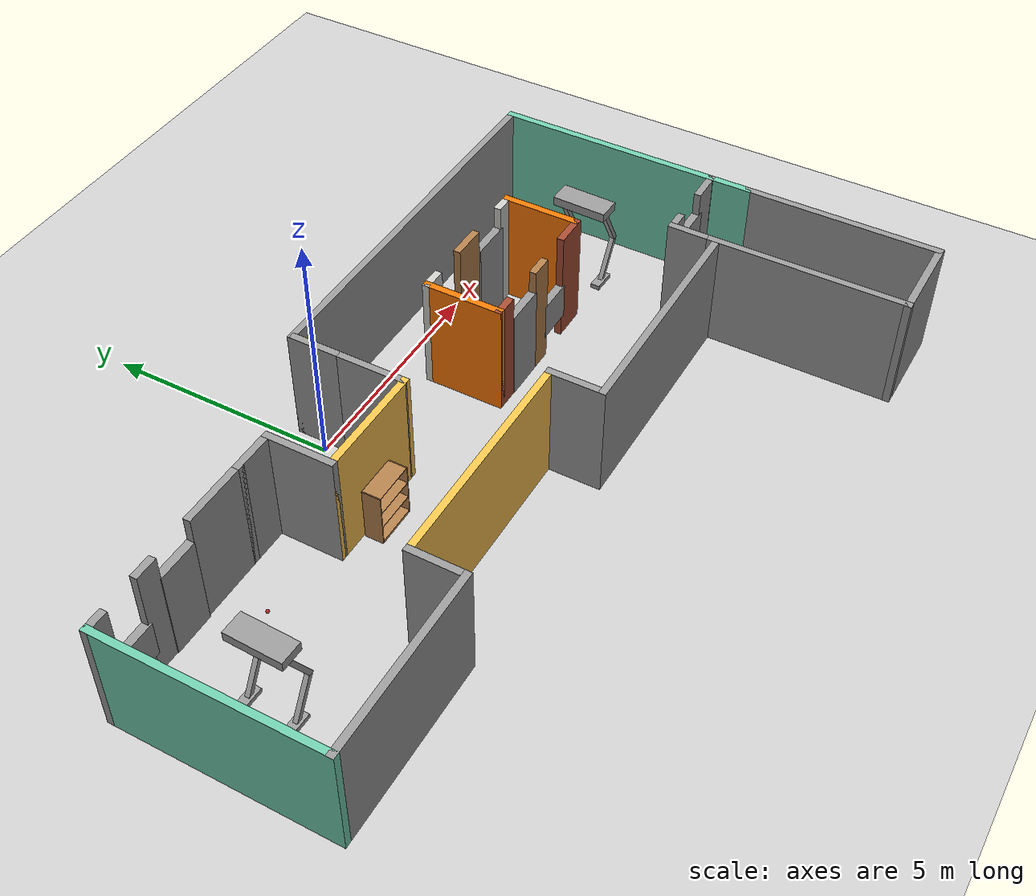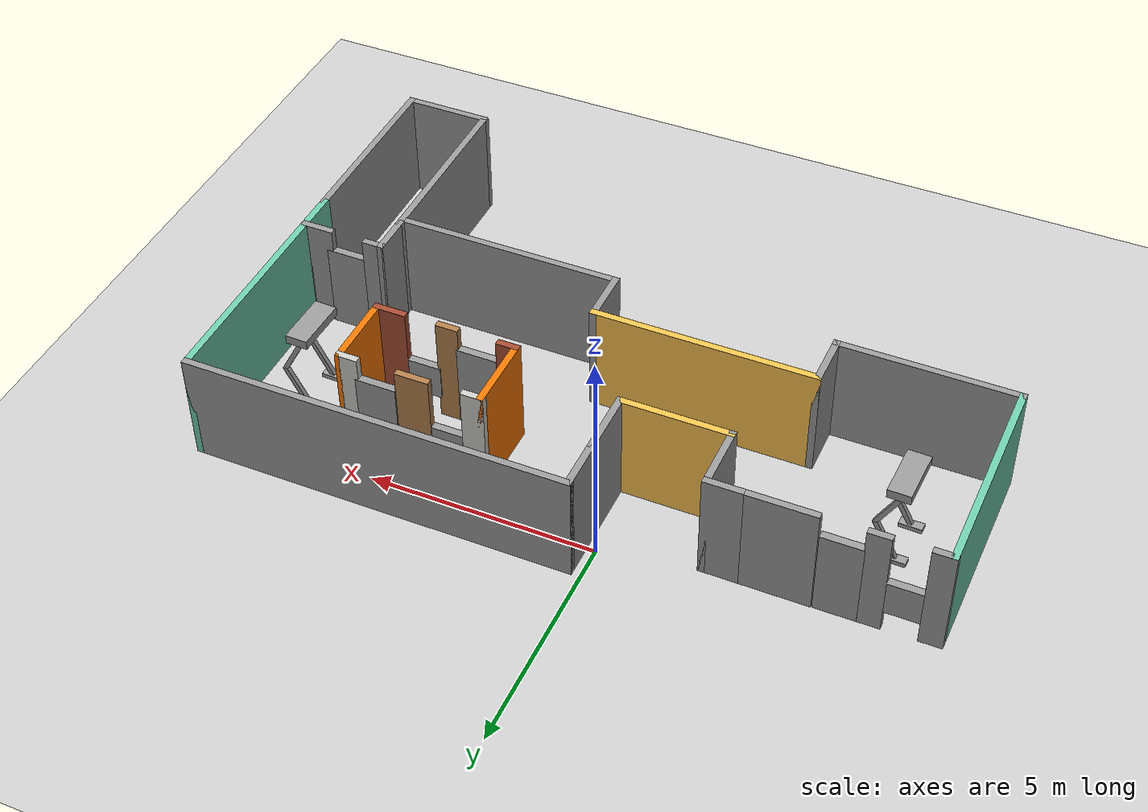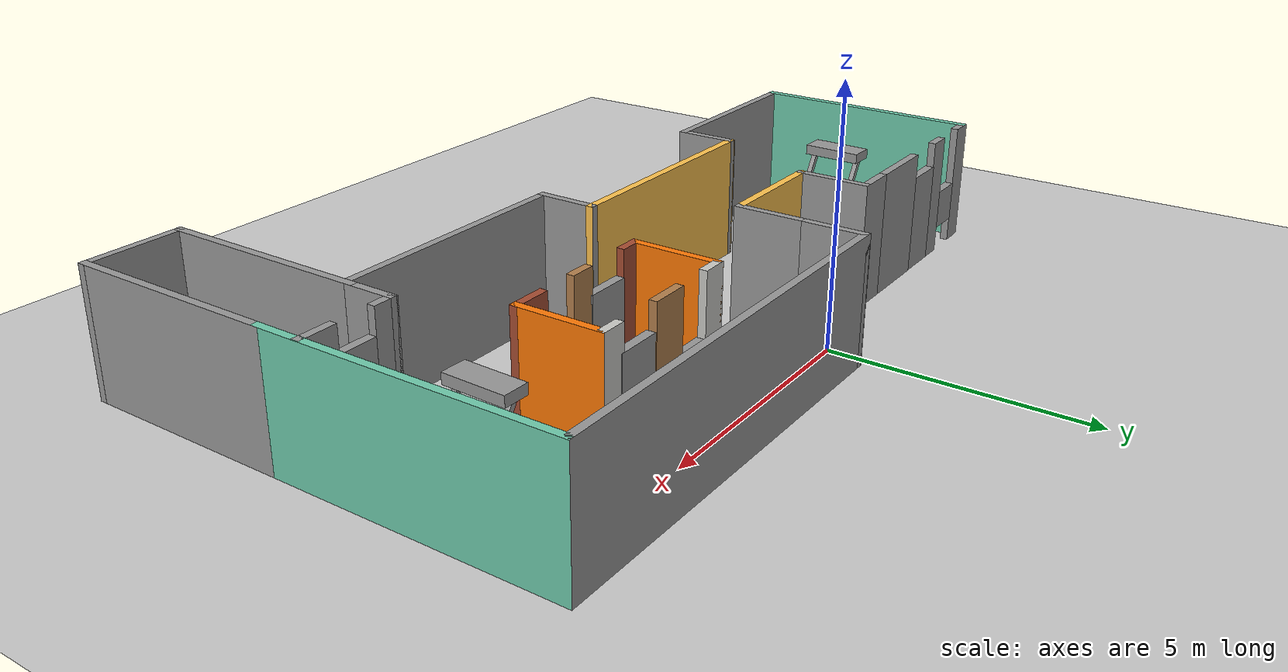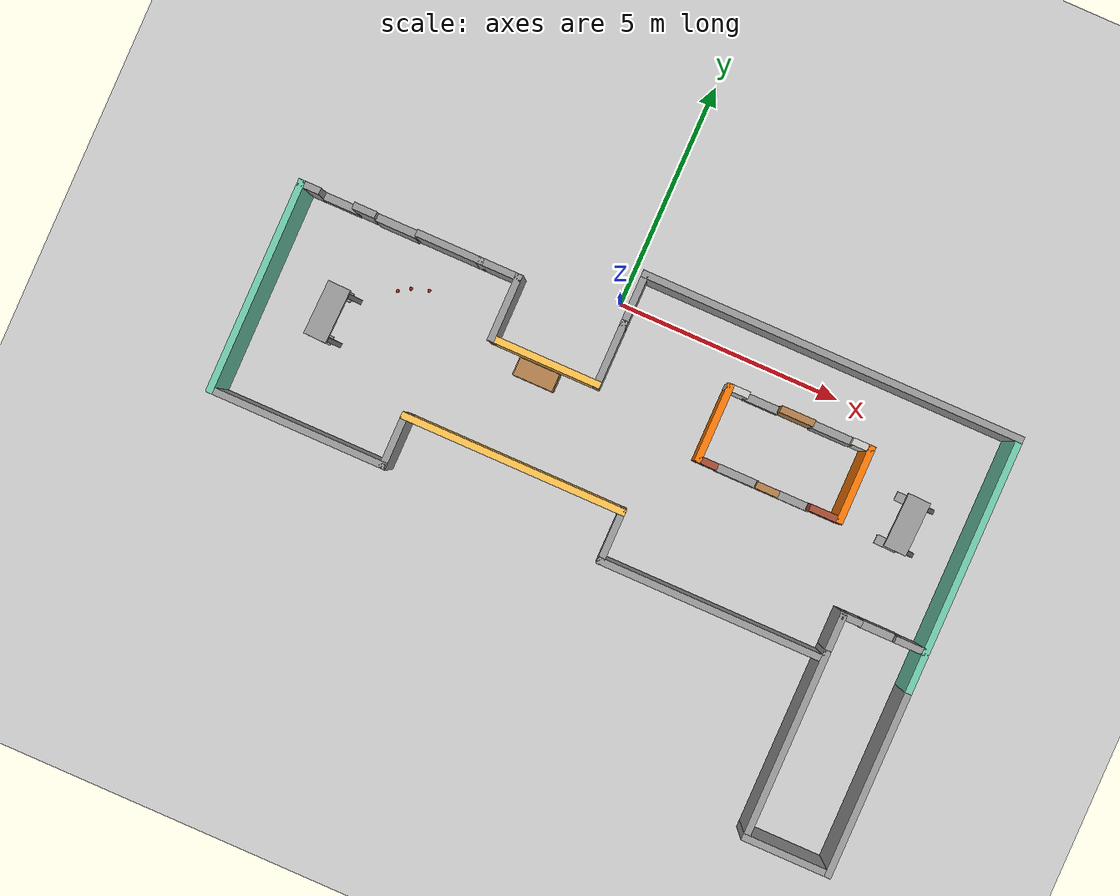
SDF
<sdf version="1.7">
 <world name="default">
  <plugin name="hello" filename="libhello.so"/>
  <light name="sun" type="directional">
   <pose>0 0 10 0 -0 0</pose>
   <diffuse>0.8 0.8 0.8 1</diffuse>
   <specular>0.2 0.2 0.2 1</specular>
   <attenuation>
    <range>1000</range>
    <constant>0.9</constant>
    <linear>0.01</linear>
    <quadratic>0.001</quadratic>
   </attenuation>
   <direction>-0.5 0.1 -0.9</direction>
   <spot><inner_angle>0</inner_angle><outer_angle>0</outer_angle><falloff>0</falloff></spot>
  </light>
  <model name="ground_plane">
   <static>1</static>
   <link name="link">
    <collision name="collision">
     <geometry><plane><normal>0 0 1</normal><size>100 100</size></plane></geometry>
     <surface>
      <contact><collide_bitmask>65535</collide_bitmask></contact>
      <friction><ode><mu>100</mu><mu2>50</mu2></ode></friction>
     </surface>
    </collision>
    <visual name="visual">
     <cast_shadows>0</cast_shadows>
     <geometry><plane><normal>0 0 1</normal><size>100 100</size></plane></geometry>
     <material>
      <script><uri>file://media/materials/scripts/gazebo.material</uri><name>Gazebo/Grey</name></script>
     </material>
    </visual>
   </link>
  </model>
  <gravity>0 0 -9.8</gravity>
  <magnetic_field>6e-06 2.3e-05 -4.2e-05</magnetic_field>
  <atmosphere type="adiabatic"/>
  <physics type="ode">
   <max_step_size>0.001</max_step_size>
   <real_time_factor>1</real_time_factor>
   <real_time_update_rate>1000</real_time_update_rate>
  </physics>
  <scene><ambient>0.4 0.4 0.4 1</ambient><background>0.7 0.7 0.7 1</background><shadows>1</shadows></scene>
  <spherical_coordinates>
   <surface_model>EARTH_WGS84</surface_model>
   <latitude_deg>0</latitude_deg>
   <longitude_deg>0</longitude_deg>
   <elevation>0</elevation>
   <heading_deg>0</heading_deg>
  </spherical_coordinates>
  <model name="Building">
   <pose>0.849011 -4.17866 0 0 -0 0</pose>
   <link name="Door_0">
    <collision name="Door_0_Collision">
     <geometry><box><size>0.9 0.17 2</size></box></geometry>
     <pose>0 0 1 0 -0 0</pose>
    </collision>
    <visual name="Door_0_Visual">
     <pose>0 0 1 0 -0 0</pose>
     <geometry><box><size>0.9 0.17 2</size></box></geometry>
     <material>
      <script><uri>file://media/materials/scripts/gazebo.material</uri><name>Gazebo/Grey</name></script>
     </material>
    </visual>
    <pose>-5.67659 3.73172 0 0 -0 0</pose>
   </link>
   <link name="Door_1">
    <collision name="Door_1_Collision">
     <geometry><box><size>0.9 0.17 2</size></box></geometry>
     <pose>0 0 1 0 -0 0</pose>
    </collision>
    <visual name="Door_1_Visual">
     <pose>0 0 1 0 -0 0</pose>
     <geometry><box><size>0.9 0.17 2</size></box></geometry>
     <material>
      <script><uri>file://media/materials/scripts/gazebo.material</uri><name>Gazebo/Grey</name></script>
     </material>
    </visual>
    <pose>2.80479 1.84268 0 0 -0 0</pose>
   </link>
   <link name="Door_2">
    <collision name="Door_2_Collision">
     <geometry><box><size>0.9 0.17 2</size></box></geometry>
     <pose>0 0 1 0 -0 0</pose>
    </collision>
    <visual name="Door_2_Visual">
     <pose>0 0 1 0 -0 0</pose>
     <geometry><box><size>0.9 0.17 2</size></box></geometry>
     <material>
      <script><uri>file://media/materials/scripts/gazebo.material</uri><name>Gazebo/Grey</name></script>
     </material>
    </visual>
    <pose>4.27081 3.44109 0 0 -0 0</pose>
   </link>
   <link name="Door_3">
    <collision name="Door_3_Collision">
     <geometry><box><size>0.9 0.17 2</size></box></geometry>
     <pose>0 0 1 0 -0 0</pose>
    </collision>
    <visual name="Door_3_Visual">
     <pose>0 0 1 0 -0 0</pose>
     <geometry><box><size>0.9 0.17 2</size></box></geometry>
     <material>
      <script><uri>file://media/materials/scripts/gazebo.material</uri><name>Gazebo/Grey</name></script>
     </material>
    </visual>
    <pose>6.77567 0.089826 0 0 -0 0</pose>
   </link>
   <link name="Wall_0">
    <collision name="Wall_0_Collision">
     <geometry><box><size>4.75 0.15 2.5</size></box></geometry>
     <pose>0 0 1.25 0 -0 0</pose>
    </collision>
    <visual name="Wall_0_Visual">
     <pose>0 0 1.25 0 -0 0</pose>
     <geometry><box><size>4.75 0.15 2.5</size></box></geometry>
     <material>
      <script><uri>file://media/materials/scripts/gazebo.material</uri><name>Gazebo/Grey</name></script>
      <ambient>0.435294 0.796078 0.67451 1</ambient>
     </material>
     <meta><layer>0</layer></meta>
    </visual>
    <pose>-7.76657 1.42597 0 0 -0 -1.5708</pose>
   </link>
   <link name="Wall_1">
    <collision name="Wall_1_Collision">
     <geometry><box><size>4 0.15 2.5</size></box></geometry>
     <pose>0 0 1.25 0 -0 0</pose>
    </collision>
    <visual name="Wall_1_Visual">
     <pose>0 0 1.25 0 -0 0</pose>
     <geometry><box><size>4 0.15 2.5</size></box></geometry>
     <material>
      <script><uri>file://media/materials/scripts/gazebo.material</uri><name>Gazebo/Grey</name></script>
      <ambient>1 1 1 1</ambient>
     </material>
     <meta><layer>0</layer></meta>
    </visual>
    <pose>-5.84157 -0.874025 0 0 -0 0</pose>
   </link>
   <link name="Wall_11">
    <collision name="Wall_11_Collision">
     <geometry><box><size>1.5 0.15 2.5</size></box></geometry>
     <pose>0 0 1.25 0 -0 0</pose>
    </collision>
    <visual name="Wall_11_Visual">
     <pose>0 0 1.25 0 -0 0</pose>
     <geometry><box><size>1.5 0.15 2.5</size></box></geometry>
     <material>
      <script><uri>file://media/materials/scripts/gazebo.material</uri><name>Gazebo/Grey</name></script>
      <ambient>1 1 1 1</ambient>
     </material>
     <meta><layer>0</layer></meta>
    </visual>
    <pose>-4.45843 3.75 0 0 -0 0</pose>
   </link>
   <link name="Wall_12">
    <collision name="Wall_12_Collision">
     <geometry><box><size>1 0.15 2.5</size></box></geometry>
     <pose>0 0 1.25 0 -0 0</pose>
    </collision>
    <visual name="Wall_12_Visual">
     <pose>0 0 1.25 0 -0 0</pose>
     <geometry><box><size>1 0.15 2.5</size></box></geometry>
     <material>
      <script><uri>file://media/materials/scripts/gazebo.material</uri><name>Gazebo/Grey</name></script>
      <ambient>1 1 1 1</ambient>
     </material>
     <meta><layer>0</layer></meta>
    </visual>
    <pose>-3.35843 3.75 0 0 -0 0</pose>
   </link>
   <link name="Wall_13">
    <collision name="Wall_13_Collision">
     <geometry><box><size>1.5 0.15 2.5</size></box></geometry>
     <pose>0 0 1.25 0 -0 0</pose>
    </collision>
    <visual name="Wall_13_Visual">
     <pose>0 0 1.25 0 -0 0</pose>
     <geometry><box><size>1.5 0.15 2.5</size></box></geometry>
     <material>
      <script><uri>file://media/materials/scripts/gazebo.material</uri><name>Gazebo/Grey</name></script>
      <ambient>1 1 1 1</ambient>
     </material>
     <meta><layer>0</layer></meta>
    </visual>
    <pose>-2.93343 3.075 0 0 -0 -1.5708</pose>
   </link>
   <link name="Wall_14">
    <collision name="Wall_14_Collision">
     <geometry><box><size>2.5 0.15 2.5</size></box></geometry>
     <pose>0 0 1.25 0 -0 0</pose>
    </collision>
    <visual name="Wall_14_Visual">
     <pose>0 0 1.25 0 -0 0</pose>
     <geometry><box><size>2.5 0.15 2.5</size></box></geometry>
     <material>
      <script><uri>file://media/materials/scripts/gazebo.material</uri><name>Gazebo/Grey</name></script>
      <ambient>1 0.764706 0.305882 1</ambient>
     </material>
     <meta><layer>0</layer></meta>
    </visual>
    <pose>-1.75843 2.4 0 0 -0 0</pose>
   </link>
   <link name="Wall_15">
    <collision name="Wall_15_Collision">
     <geometry><box><size>1.5 0.15 2.5</size></box></geometry>
     <pose>0 0 1.25 0 -0 0</pose>
    </collision>
    <visual name="Wall_15_Visual">
     <pose>0 0 1.25 0 -0 0</pose>
     <geometry><box><size>1.5 0.15 2.5</size></box></geometry>
     <material>
      <script><uri>file://media/materials/scripts/gazebo.material</uri><name>Gazebo/Grey</name></script>
      <ambient>1 1 1 1</ambient>
     </material>
     <meta><layer>0</layer></meta>
    </visual>
    <pose>-0.583428 3.075 0 0 -0 1.5708</pose>
   </link>
   <link name="Wall_16">
    <collision name="Wall_16_Collision">
     <geometry><box><size>1.25 0.15 2.5</size></box></geometry>
     <pose>0 0 1.25 0 -0 0</pose>
    </collision>
    <visual name="Wall_16_Visual">
     <pose>0 0 1.25 0 -0 0</pose>
     <geometry><box><size>1.25 0.15 2.5</size></box></geometry>
     <material>
      <script><uri>file://media/materials/scripts/gazebo.material</uri><name>Gazebo/Grey</name></script>
      <ambient>1 1 1 1</ambient>
     </material>
     <meta><layer>0</layer></meta>
    </visual>
    <pose>-0.583428 4.3 0 0 -0 1.5708</pose>
   </link>
   <link name="Wall_17">
    <collision name="Wall_17_Collision">
     <geometry><box><size>8.5 0.15 2.5</size></box></geometry>
     <pose>0 0 1.25 0 -0 0</pose>
    </collision>
    <visual name="Wall_17_Visual">
     <pose>0 0 1.25 0 -0 0</pose>
     <geometry><box><size>8.5 0.15 2.5</size></box></geometry>
     <material>
      <script><uri>file://media/materials/scripts/gazebo.material</uri><name>Gazebo/Grey</name></script>
      <ambient>1 1 1 1</ambient>
     </material>
     <meta><layer>0</layer></meta>
    </visual>
    <pose>3.59157 4.85 0 0 -0 0</pose>
   </link>
   <link name="Wall_18">
    <collision name="Wall_18_Collision">
     <geometry><box><size>5.75 0.15 2.5</size></box></geometry>
     <pose>0 0 1.25 0 -0 0</pose>
    </collision>
    <visual name="Wall_18_Visual">
     <pose>0 0 1.25 0 -0 0</pose>
     <geometry><box><size>5.75 0.15 2.5</size></box></geometry>
     <material>
      <script><uri>file://media/materials/scripts/gazebo.material</uri><name>Gazebo/Grey</name></script>
      <ambient>0.435294 0.796078 0.67451 1</ambient>
     </material>
     <meta><layer>0</layer></meta>
    </visual>
    <pose>7.76657 2.05 0 0 -0 -1.5708</pose>
   </link>
   <link name="Wall_19">
    <collision name="Wall_19_Collision">
     <geometry><box><size>4.25 0.15 2.5</size></box></geometry>
     <pose>0 0 1.25 0 -0 0</pose>
    </collision>
    <visual name="Wall_19_Visual">
     <pose>0 0 1.25 0 -0 0</pose>
     <geometry><box><size>4.25 0.15 2.5</size></box></geometry>
     <material>
      <script><uri>file://media/materials/scripts/gazebo.material</uri><name>Gazebo/Grey</name></script>
      <ambient>1 1 1 1</ambient>
     </material>
     <meta><layer>0</layer></meta>
    </visual>
    <pose>7.76657 -2.8 0 0 -0 -1.5708</pose>
   </link>
   <link name="Wall_2">
    <collision name="Wall_2_Collision">
     <geometry><box><size>1.25 0.15 2.5</size></box></geometry>
     <pose>0 0 1.25 0 -0 0</pose>
    </collision>
    <visual name="Wall_2_Visual">
     <pose>0 0 1.25 0 -0 0</pose>
     <geometry><box><size>1.25 0.15 2.5</size></box></geometry>
     <material>
      <script><uri>file://media/materials/scripts/gazebo.material</uri><name>Gazebo/Grey</name></script>
      <ambient>1 1 1 1</ambient>
     </material>
     <meta><layer>0</layer></meta>
    </visual>
    <pose>-3.91657 -0.324024 0 0 -0 1.5708</pose>
   </link>
   <link name="Wall_20">
    <collision name="Wall_20_Collision">
     <geometry><box><size>2 0.15 2.5</size></box></geometry>
     <pose>0 0 1.25 0 -0 0</pose>
    </collision>
    <visual name="Wall_20_Visual">
     <pose>0 0 1.25 0 -0 0</pose>
     <geometry><box><size>2 0.15 2.5</size></box></geometry>
     <material>
      <script><uri>file://media/materials/scripts/gazebo.material</uri><name>Gazebo/Grey</name></script>
      <ambient>1 1 1 1</ambient>
     </material>
     <meta><layer>0</layer></meta>
    </visual>
    <pose>6.84157 -4.85 0 0 -0 3.14159</pose>
   </link>
   <link name="Wall_21">
    <collision name="Wall_21_Collision">
     <geometry><box><size>4.25 0.15 2.5</size></box></geometry>
     <pose>0 0 1.25 0 -0 0</pose>
    </collision>
    <visual name="Wall_21_Visual">
     <pose>0 0 1.25 0 -0 0</pose>
     <geometry><box><size>4.25 0.15 2.5</size></box></geometry>
     <material>
      <script><uri>file://media/materials/scripts/gazebo.material</uri><name>Gazebo/Grey</name></script>
      <ambient>1 1 1 1</ambient>
     </material>
     <meta><layer>0</layer></meta>
    </visual>
    <pose>5.91657 -2.8 0 0 -0 1.5708</pose>
   </link>
   <link name="Wall_23">
    <collision name="Wall_23_Collision">
     <geometry><box><size>0.5 0.15 2.5</size></box></geometry>
     <pose>0 0 1.25 0 -0 0</pose>
    </collision>
    <visual name="Wall_23_Visual">
     <pose>0 0 1.25 0 -0 0</pose>
     <geometry><box><size>0.5 0.15 2.5</size></box></geometry>
     <material>
      <script><uri>file://media/materials/scripts/gazebo.material</uri><name>Gazebo/Wood</name></script>
      <ambient>1 1 1 1</ambient>
     </material>
     <meta><layer>0</layer></meta>
    </visual>
    <pose>3.46611 1.83381 0 0 -0 0</pose>
   </link>
   <link name="Wall_25">
    <collision name="Wall_25_Collision">
     <geometry><box><size>0.75 0.15 2.5</size></box></geometry>
     <pose>0 0 1.25 0 -0 0</pose>
    </collision>
    <visual name="Wall_25_Visual">
     <pose>0 0 1.25 0 -0 0</pose>
     <geometry><box><size>0.75 0.15 2.5</size></box></geometry>
     <material>
      <script><uri>file://media/materials/scripts/gazebo.material</uri><name>Gazebo/Wood</name></script>
      <ambient>1 1 1 1</ambient>
     </material>
     <meta><layer>0</layer></meta>
    </visual>
    <pose>3.42586 3.45216 0 0 -0 0</pose>
   </link>
   <link name="Wall_27">
    <collision name="Wall_27_Collision">
     <geometry><box><size>0.5 0.15 2.5</size></box></geometry>
     <pose>0 0 1.25 0 -0 0</pose>
    </collision>
    <visual name="Wall_27_Visual">
     <pose>0 0 1.25 0 -0 0</pose>
     <geometry><box><size>0.5 0.15 2.5</size></box></geometry>
     <material>
      <script><uri>file://media/materials/scripts/gazebo.material</uri><name>Gazebo/CeilingTiled</name></script>
      <ambient>1 1 1 1</ambient>
     </material>
     <meta><layer>0</layer></meta>
    </visual>
    <pose>2.10086 3.44216 0 0 -0 3.14159</pose>
   </link>
   <link name="Wall_28">
    <collision name="Wall_28_Collision">
     <geometry><box><size>1.75 0.15 2.5</size></box></geometry>
     <pose>0 0 1.25 0 -0 0</pose>
    </collision>
    <visual name="Wall_28_Visual">
     <pose>0 0 1.25 0 -0 0</pose>
     <geometry><box><size>1.75 0.15 2.5</size></box></geometry>
     <material>
      <script><uri>file://media/materials/scripts/gazebo.material</uri><name>Gazebo/Grey</name></script>
      <ambient>0.996078 0.47451 0.0196078 1</ambient>
     </material>
     <meta><layer>0</layer></meta>
    </visual>
    <pose>1.92586 2.64216 0 0 -0 -1.5708</pose>
   </link>
   <link name="Wall_29">
    <collision name="Wall_29_Collision">
     <geometry><box><size>0.5 0.15 2.5</size></box></geometry>
     <pose>0 0 1.25 0 -0 0</pose>
    </collision>
    <visual name="Wall_29_Visual">
     <pose>0 0 1.25 0 -0 0</pose>
     <geometry><box><size>0.5 0.15 2.5</size></box></geometry>
     <material>
      <script><uri>file://media/materials/scripts/gazebo.material</uri><name>Gazebo/Bricks</name></script>
      <ambient>1 1 1 1</ambient>
     </material>
     <meta><layer>0</layer></meta>
    </visual>
    <pose>2.10086 1.84216 0 0 -0 0</pose>
   </link>
   <link name="Wall_3">
    <collision name="Wall_3_Collision">
     <geometry><box><size>5 0.15 2.5</size></box></geometry>
     <pose>0 0 1.25 0 -0 0</pose>
    </collision>
    <visual name="Wall_3_Visual">
     <pose>0 0 1.25 0 -0 0</pose>
     <geometry><box><size>5 0.15 2.5</size></box></geometry>
     <material>
      <script><uri>file://media/materials/scripts/gazebo.material</uri><name>Gazebo/Grey</name></script>
      <ambient>1 0.764706 0.305882 1</ambient>
     </material>
     <meta><layer>0</layer></meta>
    </visual>
    <pose>-1.49157 0.225975 0 0 -0 0</pose>
   </link>
   <link name="Wall_31">
    <collision name="Wall_31_Collision">
     <geometry><box><size>0.5 0.15 2.5</size></box></geometry>
     <pose>0 0 1.25 0 -0 0</pose>
    </collision>
    <visual name="Wall_31_Visual">
     <pose>0 0 1.25 0 -0 0</pose>
     <geometry><box><size>0.5 0.15 2.5</size></box></geometry>
     <material>
      <script><uri>file://media/materials/scripts/gazebo.material</uri><name>Gazebo/CeilingTiled</name></script>
      <ambient>1 1 1 1</ambient>
     </material>
     <meta><layer>0</layer></meta>
    </visual>
    <pose>4.90086 3.44216 0 0 -0 0</pose>
   </link>
   <link name="Wall_32">
    <collision name="Wall_32_Collision">
     <geometry><box><size>1.73 0.15 2.5</size></box></geometry>
     <pose>0 0 1.25 0 -0 0</pose>
    </collision>
    <visual name="Wall_32_Visual">
     <pose>0 0 1.25 0 -0 0</pose>
     <geometry><box><size>1.73 0.15 2.5</size></box></geometry>
     <material>
      <script><uri>file://media/materials/scripts/gazebo.material</uri><name>Gazebo/Grey</name></script>
      <ambient>0.996078 0.47451 0.0196078 1</ambient>
     </material>
     <meta><layer>0</layer></meta>
    </visual>
    <pose>5.07586 2.65216 0 0 -0 -1.5708</pose>
   </link>
   <link name="Wall_33">
    <collision name="Wall_33_Collision">
     <geometry><box><size>0.75 0.15 2.5</size></box></geometry>
     <pose>0 0 1.25 0 -0 0</pose>
    </collision>
    <visual name="Wall_33_Visual">
     <pose>0 0 1.25 0 -0 0</pose>
     <geometry><box><size>0.75 0.15 2.5</size></box></geometry>
     <material>
      <script><uri>file://media/materials/scripts/gazebo.material</uri><name>Gazebo/Bricks</name></script>
      <ambient>1 1 1 1</ambient>
     </material>
     <meta><layer>0</layer></meta>
    </visual>
    <pose>4.77586 1.85216 0 0 -0 3.14159</pose>
   </link>
   <link name="Wall_35">
    <collision name="Wall_35_Collision">
     <geometry><box><size>1 0.15 2.5</size></box></geometry>
     <pose>0 0 1.25 0 -0 0</pose>
    </collision>
    <visual name="Wall_35_Visual">
     <pose>0 0 1.25 0 -0 0</pose>
     <geometry><box><size>1 0.15 2.5</size></box></geometry>
     <material>
      <script><uri>file://media/materials/scripts/gazebo.material</uri><name>Gazebo/Grey</name></script>
      <ambient>1 1 1 1</ambient>
     </material>
     <meta><layer>0</layer></meta>
    </visual>
    <pose>5.91657 -0.325 0 0 -0 1.5708</pose>
   </link>
   <link name="Wall_36">
    <collision name="Wall_36_Collision">
     <geometry><box><size>0.5 0.15 2.5</size></box></geometry>
     <pose>0 0 1.25 0 -0 0</pose>
    </collision>
    <visual name="Wall_36_Visual">
     <pose>0 0 1.25 0 -0 0</pose>
     <geometry><box><size>0.5 0.15 2.5</size></box></geometry>
     <material>
      <script><uri>file://media/materials/scripts/gazebo.material</uri><name>Gazebo/Grey</name></script>
      <ambient>1 1 1 1</ambient>
     </material>
     <meta><layer>0</layer></meta>
    </visual>
    <pose>6.09157 0.1 0 0 -0 0</pose>
   </link>
   <link name="Wall_38">
    <collision name="Wall_38_Collision">
     <geometry><box><size>0.75 0.15 2.5</size></box></geometry>
     <pose>0 0 1.25 0 -0 0</pose>
    </collision>
    <visual name="Wall_38_Visual">
     <pose>0 0 1.25 0 -0 0</pose>
     <geometry><box><size>0.75 0.15 2.5</size></box></geometry>
     <material>
      <script><uri>file://media/materials/scripts/gazebo.material</uri><name>Gazebo/Grey</name></script>
      <ambient>1 1 1 1</ambient>
     </material>
     <meta><layer>0</layer></meta>
    </visual>
    <pose>7.45865 0.087042 0 0 -0 0</pose>
   </link>
   <link name="Wall_39">
    <collision name="Wall_39_Collision">
     <geometry><box><size>0.15 0.15 2.5</size></box></geometry>
     <pose>0 0 1.25 0 -0 0</pose>
    </collision>
    <visual name="Wall_39_Visual">
     <pose>0 0 1.25 0 -0 0</pose>
     <geometry><box><size>0.15 0.15 2.5</size></box></geometry>
     <material>
      <script><uri>file://media/materials/scripts/gazebo.material</uri><name>Gazebo/Grey</name></script>
      <ambient>1 1 1 1</ambient>
     </material>
     <meta><layer>0</layer></meta>
    </visual>
    <pose>7.74995 0.087042 0 0 -0 0</pose>
   </link>
   <link name="Wall_4">
    <collision name="Wall_4_Collision">
     <geometry><box><size>1.25 0.15 2.5</size></box></geometry>
     <pose>0 0 1.25 0 -0 0</pose>
    </collision>
    <visual name="Wall_4_Visual">
     <pose>0 0 1.25 0 -0 0</pose>
     <geometry><box><size>1.25 0.15 2.5</size></box></geometry>
     <material>
      <script><uri>file://media/materials/scripts/gazebo.material</uri><name>Gazebo/Grey</name></script>
      <ambient>1 1 1 1</ambient>
     </material>
     <meta><layer>0</layer></meta>
    </visual>
    <pose>0.933427 -0.324024 0 0 -0 -1.5708</pose>
   </link>
   <link name="Wall_40">
    <collision name="Wall_40_Collision">
     <geometry><box><size>0.15 0.15 2.5</size></box></geometry>
     <pose>0 0 1.25 0 -0 0</pose>
    </collision>
    <visual name="Wall_40_Visual">
     <pose>0 0 1.25 0 -0 0</pose>
     <geometry><box><size>0.15 0.15 2.5</size></box></geometry>
     <material>
      <script><uri>file://media/materials/scripts/gazebo.material</uri><name>Gazebo/Grey</name></script>
      <ambient>1 1 1 1</ambient>
     </material>
     <meta><layer>0</layer></meta>
    </visual>
    <pose>7.74995 0.087042 0 0 -0 0</pose>
   </link>
   <link name="Wall_41">
    <collision name="Wall_41_Collision">
     <geometry><box><size>0.15 0.15 2.5</size></box></geometry>
     <pose>0 0 1.25 0 -0 0</pose>
    </collision>
    <visual name="Wall_41_Visual">
     <pose>0 0 1.25 0 -0 0</pose>
     <geometry><box><size>0.15 0.15 2.5</size></box></geometry>
     <material>
      <script><uri>file://media/materials/scripts/gazebo.material</uri><name>Gazebo/Grey</name></script>
      <ambient>1 1 1 1</ambient>
     </material>
     <meta><layer>0</layer></meta>
    </visual>
    <pose>7.74995 0.087042 0 0 -0 0</pose>
   </link>
   <link name="Wall_5">
    <collision name="Wall_5_Collision">
     <geometry><box><size>5 0.15 2.5</size></box></geometry>
     <pose>0 0 1.25 0 -0 0</pose>
    </collision>
    <visual name="Wall_5_Visual">
     <pose>0 0 1.25 0 -0 0</pose>
     <geometry><box><size>5 0.15 2.5</size></box></geometry>
     <material>
      <script><uri>file://media/materials/scripts/gazebo.material</uri><name>Gazebo/Grey</name></script>
      <ambient>1 1 1 1</ambient>
     </material>
     <meta><layer>0</layer></meta>
    </visual>
    <pose>3.35843 -0.874025 0 0 -0 0</pose>
   </link>
   <link name="Wall_7">
    <collision name="Wall_7_Collision">
     <geometry><box><size>0.5 0.15 2.5</size></box></geometry>
     <pose>0 0 1.25 0 -0 0</pose>
    </collision>
    <visual name="Wall_7_Visual">
     <pose>0 0 1.25 0 -0 0</pose>
     <geometry><box><size>0.5 0.15 2.5</size></box></geometry>
     <material>
      <script><uri>file://media/materials/scripts/gazebo.material</uri><name>Gazebo/Grey</name></script>
      <ambient>1 1 1 1</ambient>
     </material>
     <meta><layer>0</layer></meta>
    </visual>
    <pose>-7.59157 3.72598 0 0 -0 0</pose>
   </link>
   <link name="Wall_9">
    <collision name="Wall_9_Collision">
     <geometry><box><size>0.5 0.15 2.5</size></box></geometry>
     <pose>0 0 1.25 0 -0 0</pose>
    </collision>
    <visual name="Wall_9_Visual">
     <pose>0 0 1.25 0 -0 0</pose>
     <geometry><box><size>0.5 0.15 2.5</size></box></geometry>
     <material>
      <script><uri>file://media/materials/scripts/gazebo.material</uri><name>Gazebo/Grey</name></script>
      <ambient>1 1 1 1</ambient>
     </material>
     <meta><layer>0</layer></meta>
    </visual>
    <pose>-6.35633 3.7397 0 0 -0 0</pose>
   </link>
   <link name="Window_0">
    <collision name="Window_0_Collision">
     <geometry><box><size>0.8 0.17 0.8</size></box></geometry>
     <pose>0 0 0.4 0 -0 0</pose>
    </collision>
    <visual name="Window_0_Visual">
     <pose>0 0 0.4 0 -0 0</pose>
     <geometry><box><size>0.8 0.17 0.8</size></box></geometry>
     <material>
      <script><uri>file://media/materials/scripts/gazebo.material</uri><name>Gazebo/Grey</name></script>
     </material>
    </visual>
    <pose>-6.94222 3.72169 0.5 0 -0 0</pose>
   </link>
   <link name="Window_1">
    <collision name="Window_1_Collision">
     <geometry><box><size>0.8 0.17 0.8</size></box></geometry>
     <pose>0 0 0.4 0 -0 0</pose>
    </collision>
    <visual name="Window_1_Visual">
     <pose>0 0 0.4 0 -0 0</pose>
     <geometry><box><size>0.8 0.17 0.8</size></box></geometry>
     <material>
      <script><uri>file://media/materials/scripts/gazebo.material</uri><name>Gazebo/Grey</name></script>
     </material>
    </visual>
    <pose>4.06227 1.84065 0.5 0 -0 0</pose>
   </link>
   <link name="Window_2">
    <collision name="Window_2_Collision">
     <geometry><box><size>0.8 0.17 0.8</size></box></geometry>
     <pose>0 0 0.4 0 -0 0</pose>
    </collision>
    <visual name="Window_2_Visual">
     <pose>0 0 0.4 0 -0 0</pose>
     <geometry><box><size>0.8 0.17 0.8</size></box></geometry>
     <material>
      <script><uri>file://media/materials/scripts/gazebo.material</uri><name>Gazebo/Grey</name></script>
     </material>
    </visual>
    <pose>2.6882 3.43109 0.5 0 -0 0</pose>
   </link>
   <static>1</static>
  </model>
  <model name="HumanoidRobot">
   <link name="link_0">
    <inertial>
     <mass>1</mass>
     <inertia>
      <ixx>0.166667</ixx>
      <ixy>0</ixy>
      <ixz>0</ixz>
      <iyy>0.166667</iyy>
      <iyz>0</iyz>
      <izz>0.166667</izz>
     </inertia>
    </inertial>
    <pose>-2.93875 -4.13679 -0.426059 0 -0 0</pose>
    <visual name="visual">
     <geometry><box><size>0.5 0.2 0.1</size></box></geometry>
     <material>
      <lighting>1</lighting>
      <script><uri>file://media/materials/scripts/gazebo.material</uri><name>Gazebo/Grey</name></script>
      <shader type="pixel"><normal_map>__default__</normal_map></shader>
      <ambient>0.3 0.3 0.3 1</ambient>
      <diffuse>0.7 0.7 0.7 1</diffuse>
      <specular>0.01 0.01 0.01 1</specular>
      <emissive>0 0 0 1</emissive>
     </material>
    </visual>
    <collision name="collision">
     <geometry><box><size>0.5 0.2 0.1</size></box></geometry>
     <surface>
      <friction>
       <ode><mu>1</mu><mu2>1</mu2><fdir1>0 0 0</fdir1><slip1>0</slip1><slip2>0</slip2></ode>
       <torsional>
        <coefficient>1</coefficient>
        <patch_radius>0</patch_radius>
        <surface_radius>0</surface_radius>
        <use_patch_radius>1</use_patch_radius>
        <ode><slip>0</slip></ode>
       </torsional>
      </friction>
      <bounce><restitution_coefficient>0</restitution_coefficient><threshold>1e+06</threshold></bounce>
      <contact>
       <collide_without_contact>0</collide_without_contact>
       <collide_without_contact_bitmask>1</collide_without_contact_bitmask>
       <collide_bitmask>1</collide_bitmask>
       <ode>
        <soft_cfm>0</soft_cfm>
        <soft_erp>0.2</soft_erp>
        <kp>1e+13</kp>
        <kd>1</kd>
        <max_vel>0.01</max_vel>
        <min_depth>0</min_depth>
       </ode>
       <bullet>
        <split_impulse>1</split_impulse>
        <split_impulse_penetration_threshold>-0.01</split_impulse_penetration_threshold>
        <soft_cfm>0</soft_cfm>
        <soft_erp>0.2</soft_erp>
        <kp>1e+13</kp>
        <kd>1</kd>
       </bullet>
      </contact>
     </surface>
    </collision>
   </link>
   <link name="link_0_clone">
    <inertial>
     <mass>1</mass>
     <inertia>
      <ixx>0.166667</ixx>
      <ixy>0</ixy>
      <ixz>0</ixz>
      <iyy>0.166667</iyy>
      <iyz>0</iyz>
      <izz>0.166667</izz>
     </inertia>
    </inertial>
    <pose>-2.93875 -3.13679 -0.426059 0 -0 0</pose>
    <visual name="visual">
     <geometry><box><size>0.5 0.2 0.1</size></box></geometry>
     <material>
      <lighting>1</lighting>
      <script><uri>file://media/materials/scripts/gazebo.material</uri><name>Gazebo/Grey</name></script>
      <shader type="pixel"><normal_map>__default__</normal_map></shader>
      <ambient>0.3 0.3 0.3 1</ambient>
      <diffuse>0.7 0.7 0.7 1</diffuse>
      <specular>0.01 0.01 0.01 1</specular>
      <emissive>0 0 0 1</emissive>
     </material>
    </visual>
    <collision name="collision">
     <geometry><box><size>0.5 0.2 0.1</size></box></geometry>
     <surface>
      <friction>
       <ode><mu>1</mu><mu2>1</mu2><fdir1>0 0 0</fdir1><slip1>0</slip1><slip2>0</slip2></ode>
       <torsional>
        <coefficient>1</coefficient>
        <patch_radius>0</patch_radius>
        <surface_radius>0</surface_radius>
        <use_patch_radius>1</use_patch_radius>
        <ode><slip>0</slip></ode>
       </torsional>
      </friction>
      <bounce><restitution_coefficient>0</restitution_coefficient><threshold>1e+06</threshold></bounce>
      <contact>
       <collide_without_contact>0</collide_without_contact>
       <collide_without_contact_bitmask>1</collide_without_contact_bitmask>
       <collide_bitmask>1</collide_bitmask>
       <ode>
        <soft_cfm>0</soft_cfm>
        <soft_erp>0.2</soft_erp>
        <kp>1e+13</kp>
        <kd>1</kd>
        <max_vel>0.01</max_vel>
        <min_depth>0</min_depth>
       </ode>
       <bullet>
        <split_impulse>1</split_impulse>
        <split_impulse_penetration_threshold>-0.01</split_impulse_penetration_threshold>
        <soft_cfm>0</soft_cfm>
        <soft_erp>0.2</soft_erp>
        <kp>1e+13</kp>
        <kd>1</kd>
       </bullet>
      </contact>
     </surface>
    </collision>
   </link>
   <link name="link_1">
    <inertial>
     <mass>1</mass>
     <inertia>
      <ixx>0.166667</ixx>
      <ixy>0</ixy>
      <ixz>0</ixz>
      <iyy>0.166667</iyy>
      <iyz>0</iyz>
      <izz>0.166667</izz>
     </inertia>
    </inertial>
    <pose>-2.68875 -4.13679 0.023941 0 0.5 0</pose>
    <visual name="visual">
     <geometry><box><size>0.1 0.1 1</size></box></geometry>
     <material>
      <lighting>1</lighting>
      <script><uri>file://media/materials/scripts/gazebo.material</uri><name>Gazebo/Grey</name></script>
      <shader type="pixel"><normal_map>__default__</normal_map></shader>
      <ambient>0.3 0.3 0.3 1</ambient>
      <diffuse>0.7 0.7 0.7 1</diffuse>
      <specular>0.01 0.01 0.01 1</specular>
      <emissive>0 0 0 1</emissive>
     </material>
    </visual>
    <collision name="collision">
     <geometry><box><size>0.1 0.1 1</size></box></geometry>
     <surface>
      <friction>
       <ode><mu>1</mu><mu2>1</mu2><fdir1>0 0 0</fdir1><slip1>0</slip1><slip2>0</slip2></ode>
       <torsional>
        <coefficient>1</coefficient>
        <patch_radius>0</patch_radius>
        <surface_radius>0</surface_radius>
        <use_patch_radius>1</use_patch_radius>
        <ode><slip>0</slip></ode>
       </torsional>
      </friction>
      <bounce><restitution_coefficient>0</restitution_coefficient><threshold>1e+06</threshold></bounce>
      <contact>
       <collide_without_contact>0</collide_without_contact>
       <collide_without_contact_bitmask>1</collide_without_contact_bitmask>
       <collide_bitmask>1</collide_bitmask>
       <ode>
        <soft_cfm>0</soft_cfm>
        <soft_erp>0.2</soft_erp>
        <kp>1e+13</kp>
        <kd>1</kd>
        <max_vel>0.01</max_vel>
        <min_depth>0</min_depth>
       </ode>
       <bullet>
        <split_impulse>1</split_impulse>
        <split_impulse_penetration_threshold>-0.01</split_impulse_penetration_threshold>
        <soft_cfm>0</soft_cfm>
        <soft_erp>0.2</soft_erp>
        <kp>1e+13</kp>
        <kd>1</kd>
       </bullet>
      </contact>
     </surface>
    </collision>
   </link>
   <link name="link_1_clone">
    <inertial>
     <mass>1</mass>
     <inertia>
      <ixx>0.166667</ixx>
      <ixy>0</ixy>
      <ixz>0</ixz>
      <iyy>0.166667</iyy>
      <iyz>0</iyz>
      <izz>0.166667</izz>
     </inertia>
    </inertial>
    <pose>-2.68875 -3.13679 0.023941 0 0.5 0</pose>
    <visual name="visual">
     <geometry><box><size>0.1 0.1 1</size></box></geometry>
     <material>
      <lighting>1</lighting>
      <script><uri>file://media/materials/scripts/gazebo.material</uri><name>Gazebo/Grey</name></script>
      <shader type="pixel"><normal_map>__default__</normal_map></shader>
      <ambient>0.3 0.3 0.3 1</ambient>
      <diffuse>0.7 0.7 0.7 1</diffuse>
      <specular>0.01 0.01 0.01 1</specular>
      <emissive>0 0 0 1</emissive>
     </material>
    </visual>
    <collision name="collision">
     <geometry><box><size>0.1 0.1 1</size></box></geometry>
     <surface>
      <friction>
       <ode><mu>1</mu><mu2>1</mu2><fdir1>0 0 0</fdir1><slip1>0</slip1><slip2>0</slip2></ode>
       <torsional>
        <coefficient>1</coefficient>
        <patch_radius>0</patch_radius>
        <surface_radius>0</surface_radius>
        <use_patch_radius>1</use_patch_radius>
        <ode><slip>0</slip></ode>
       </torsional>
      </friction>
      <bounce><restitution_coefficient>0</restitution_coefficient><threshold>1e+06</threshold></bounce>
      <contact>
       <collide_without_contact>0</collide_without_contact>
       <collide_without_contact_bitmask>1</collide_without_contact_bitmask>
       <collide_bitmask>1</collide_bitmask>
       <ode>
        <soft_cfm>0</soft_cfm>
        <soft_erp>0.2</soft_erp>
        <kp>1e+13</kp>
        <kd>1</kd>
        <max_vel>0.01</max_vel>
        <min_depth>0</min_depth>
       </ode>
       <bullet>
        <split_impulse>1</split_impulse>
        <split_impulse_penetration_threshold>-0.01</split_impulse_penetration_threshold>
        <soft_cfm>0</soft_cfm>
        <soft_erp>0.2</soft_erp>
        <kp>1e+13</kp>
        <kd>1</kd>
       </bullet>
      </contact>
     </surface>
    </collision>
   </link>
   <link name="link_2">
    <inertial>
     <mass>1</mass>
     <inertia>
      <ixx>0.166667</ixx>
      <ixy>0</ixy>
      <ixz>0</ixz>
      <iyy>0.166667</iyy>
      <iyz>0</iyz>
      <izz>0.166667</izz>
     </inertia>
    </inertial>
    <pose>-2.68022 -4.13679 0.873898 0 -0.5 0</pose>
    <visual name="visual">
     <geometry><box><size>0.1 0.1 1</size></box></geometry>
     <material>
      <lighting>1</lighting>
      <script><uri>file://media/materials/scripts/gazebo.material</uri><name>Gazebo/Grey</name></script>
      <shader type="pixel"><normal_map>__default__</normal_map></shader>
      <ambient>0.3 0.3 0.3 1</ambient>
      <diffuse>0.7 0.7 0.7 1</diffuse>
      <specular>0.01 0.01 0.01 1</specular>
      <emissive>0 0 0 1</emissive>
     </material>
    </visual>
    <collision name="collision">
     <geometry><box><size>0.1 0.1 1</size></box></geometry>
     <surface>
      <friction>
       <ode><mu>1</mu><mu2>1</mu2><fdir1>0 0 0</fdir1><slip1>0</slip1><slip2>0</slip2></ode>
       <torsional>
        <coefficient>1</coefficient>
        <patch_radius>0</patch_radius>
        <surface_radius>0</surface_radius>
        <use_patch_radius>1</use_patch_radius>
        <ode><slip>0</slip></ode>
       </torsional>
      </friction>
      <bounce><restitution_coefficient>0</restitution_coefficient><threshold>1e+06</threshold></bounce>
      <contact>
       <collide_without_contact>0</collide_without_contact>
       <collide_without_contact_bitmask>1</collide_without_contact_bitmask>
       <collide_bitmask>1</collide_bitmask>
       <ode>
        <soft_cfm>0</soft_cfm>
        <soft_erp>0.2</soft_erp>
        <kp>1e+13</kp>
        <kd>1</kd>
        <max_vel>0.01</max_vel>
        <min_depth>0</min_depth>
       </ode>
       <bullet>
        <split_impulse>1</split_impulse>
        <split_impulse_penetration_threshold>-0.01</split_impulse_penetration_threshold>
        <soft_cfm>0</soft_cfm>
        <soft_erp>0.2</soft_erp>
        <kp>1e+13</kp>
        <kd>1</kd>
       </bullet>
      </contact>
     </surface>
    </collision>
   </link>
   <link name="link_2_clone">
    <inertial>
     <mass>1</mass>
     <inertia>
      <ixx>0.166667</ixx>
      <ixy>0</ixy>
      <ixz>0</ixz>
      <iyy>0.166667</iyy>
      <iyz>0</iyz>
      <izz>0.166667</izz>
     </inertia>
    </inertial>
    <pose>-2.68022 -3.13679 0.873898 0 -0.5 0</pose>
    <visual name="visual">
     <geometry><box><size>0.1 0.1 1</size></box></geometry>
     <material>
      <lighting>1</lighting>
      <script><uri>file://media/materials/scripts/gazebo.material</uri><name>Gazebo/Grey</name></script>
      <shader type="pixel"><normal_map>__default__</normal_map></shader>
      <ambient>0.3 0.3 0.3 1</ambient>
      <diffuse>0.7 0.7 0.7 1</diffuse>
      <specular>0.01 0.01 0.01 1</specular>
      <emissive>0 0 0 1</emissive>
     </material>
    </visual>
    <collision name="collision">
     <geometry><box><size>0.1 0.1 1</size></box></geometry>
     <surface>
      <friction>
       <ode><mu>1</mu><mu2>1</mu2><fdir1>0 0 0</fdir1><slip1>0</slip1><slip2>0</slip2></ode>
       <torsional>
        <coefficient>1</coefficient>
        <patch_radius>0</patch_radius>
        <surface_radius>0</surface_radius>
        <use_patch_radius>1</use_patch_radius>
        <ode><slip>0</slip></ode>
       </torsional>
      </friction>
      <bounce><restitution_coefficient>0</restitution_coefficient><threshold>1e+06</threshold></bounce>
      <contact>
       <collide_without_contact>0</collide_without_contact>
       <collide_without_contact_bitmask>1</collide_without_contact_bitmask>
       <collide_bitmask>1</collide_bitmask>
       <ode>
        <soft_cfm>0</soft_cfm>
        <soft_erp>0.2</soft_erp>
        <kp>1e+13</kp>
        <kd>1</kd>
        <max_vel>0.01</max_vel>
        <min_depth>0</min_depth>
       </ode>
       <bullet>
        <split_impulse>1</split_impulse>
        <split_impulse_penetration_threshold>-0.01</split_impulse_penetration_threshold>
        <soft_cfm>0</soft_cfm>
        <soft_erp>0.2</soft_erp>
        <kp>1e+13</kp>
        <kd>1</kd>
       </bullet>
      </contact>
     </surface>
    </collision>
   </link>
   <link name="link_4">
    <inertial>
     <mass>1</mass>
     <inertia>
      <ixx>0.166667</ixx>
      <ixy>0</ixy>
      <ixz>0</ixz>
      <iyy>0.166667</iyy>
      <iyz>0</iyz>
      <izz>0.166667</izz>
     </inertia>
    </inertial>
    <pose>-2.87278 -3.62138 1.41019 0 -0 0</pose>
    <visual name="visual">
     <geometry><box><size>0.5 1.2 0.2</size></box></geometry>
     <material>
      <lighting>1</lighting>
      <script><uri>file://media/materials/scripts/gazebo.material</uri><name>Gazebo/Grey</name></script>
      <shader type="pixel"><normal_map>__default__</normal_map></shader>
      <ambient>0.3 0.3 0.3 1</ambient>
      <diffuse>0.7 0.7 0.7 1</diffuse>
      <specular>0.01 0.01 0.01 1</specular>
      <emissive>0 0 0 1</emissive>
     </material>
    </visual>
    <collision name="collision">
     <geometry><box><size>0.5 1.2 0.2</size></box></geometry>
     <surface>
      <friction>
       <ode><mu>1</mu><mu2>1</mu2><fdir1>0 0 0</fdir1><slip1>0</slip1><slip2>0</slip2></ode>
       <torsional>
        <coefficient>1</coefficient>
        <patch_radius>0</patch_radius>
        <surface_radius>0</surface_radius>
        <use_patch_radius>1</use_patch_radius>
        <ode><slip>0</slip></ode>
       </torsional>
      </friction>
      <bounce><restitution_coefficient>0</restitution_coefficient><threshold>1e+06</threshold></bounce>
      <contact>
       <collide_without_contact>0</collide_without_contact>
       <collide_without_contact_bitmask>1</collide_without_contact_bitmask>
       <collide_bitmask>1</collide_bitmask>
       <ode>
        <soft_cfm>0</soft_cfm>
        <soft_erp>0.2</soft_erp>
        <kp>1e+13</kp>
        <kd>1</kd>
        <max_vel>0.01</max_vel>
        <min_depth>0</min_depth>
       </ode>
       <bullet>
        <split_impulse>1</split_impulse>
        <split_impulse_penetration_threshold>-0.01</split_impulse_penetration_threshold>
        <soft_cfm>0</soft_cfm>
        <soft_erp>0.2</soft_erp>
        <kp>1e+13</kp>
        <kd>1</kd>
       </bullet>
      </contact>
     </surface>
    </collision>
   </link>
   <joint name="link_0_JOINT_1" type="revolute">
    <parent>link_0</parent>
    <child>link_1</child>
    <axis>
     <xyz>0 0 1</xyz>
     <limit>
      <lower>-1.79769e+308</lower>
      <upper>1.79769e+308</upper>
      <effort>-1</effort>
      <velocity>-1</velocity>
     </limit>
     <dynamics>
      <spring_reference>0</spring_reference>
      <spring_stiffness>0</spring_stiffness>
      <damping>0</damping>
     </dynamics>
    </axis>
    <physics>
     <ode><limit><cfm>0</cfm><erp>0.2</erp></limit><suspension><cfm>0</cfm><erp>0.2</erp></suspension></ode>
    </physics>
   </joint>
   <joint name="link_0_clone_JOINT_2" type="revolute">
    <parent>link_0_clone</parent>
    <child>link_1_clone</child>
    <axis>
     <xyz>0 0 1</xyz>
     <limit>
      <lower>-1.79769e+308</lower>
      <upper>1.79769e+308</upper>
      <effort>-1</effort>
      <velocity>-1</velocity>
     </limit>
     <dynamics>
      <spring_reference>0</spring_reference>
      <spring_stiffness>0</spring_stiffness>
      <damping>0</damping>
     </dynamics>
    </axis>
    <physics>
     <ode><limit><cfm>0</cfm><erp>0.2</erp></limit><suspension><cfm>0</cfm><erp>0.2</erp></suspension></ode>
    </physics>
   </joint>
   <joint name="link_1_JOINT_3" type="revolute">
    <parent>link_1</parent>
    <child>link_2</child>
    <axis>
     <xyz>0 0 1</xyz>
     <limit>
      <lower>-1.79769e+308</lower>
      <upper>1.79769e+308</upper>
      <effort>-1</effort>
      <velocity>-1</velocity>
     </limit>
     <dynamics>
      <spring_reference>0</spring_reference>
      <spring_stiffness>0</spring_stiffness>
      <damping>0</damping>
     </dynamics>
    </axis>
    <physics>
     <ode><limit><cfm>0</cfm><erp>0.2</erp></limit><suspension><cfm>0</cfm><erp>0.2</erp></suspension></ode>
    </physics>
   </joint>
   <joint name="link_1_clone_JOINT_4" type="revolute">
    <parent>link_1_clone</parent>
    <child>link_2_clone</child>
    <axis>
     <xyz>0 0 1</xyz>
     <limit>
      <lower>-1.79769e+308</lower>
      <upper>1.79769e+308</upper>
      <effort>-1</effort>
      <velocity>-1</velocity>
     </limit>
     <dynamics>
      <spring_reference>0</spring_reference>
      <spring_stiffness>0</spring_stiffness>
      <damping>0</damping>
     </dynamics>
    </axis>
    <physics>
     <ode><limit><cfm>0</cfm><erp>0.2</erp></limit><suspension><cfm>0</cfm><erp>0.2</erp></suspension></ode>
    </physics>
   </joint>
   <joint name="link_4_JOINT_6" type="revolute">
    <parent>link_4</parent>
    <child>link_2</child>
    <axis>
     <xyz>1 0 0</xyz>
     <limit>
      <lower>-1.79769e+308</lower>
      <upper>1.79769e+308</upper>
      <effort>-1</effort>
      <velocity>-1</velocity>
     </limit>
     <dynamics>
      <spring_reference>0</spring_reference>
      <spring_stiffness>0</spring_stiffness>
      <damping>0</damping>
     </dynamics>
    </axis>
    <physics>
     <ode><limit><cfm>0</cfm><erp>0.2</erp></limit><suspension><cfm>0</cfm><erp>0.2</erp></suspension></ode>
    </physics>
   </joint>
   <joint name="link_4_JOINT_7" type="revolute">
    <parent>link_4</parent>
    <child>link_2_clone</child>
    <axis>
     <xyz>1 0 0</xyz>
     <limit>
      <lower>-1.79769e+308</lower>
      <upper>1.79769e+308</upper>
      <effort>-1</effort>
      <velocity>-1</velocity>
     </limit>
     <dynamics>
      <spring_reference>0</spring_reference>
      <spring_stiffness>0</spring_stiffness>
      <damping>0</damping>
     </dynamics>
    </axis>
    <physics>
     <ode><limit><cfm>0</cfm><erp>0.2</erp></limit><suspension><cfm>0</cfm><erp>0.2</erp></suspension></ode>
    </physics>
   </joint>
   <static>0</static>
   <pose>-2.446 0.898907 0.475756 0 0.000112 -0.028533</pose>
  </model>
  <model name="HumanoidRobot_0">
   <link name="link_0">
    <inertial>
     <mass>1</mass>
     <inertia>
      <ixx>0.166667</ixx>
      <ixy>0</ixy>
      <ixz>0</ixz>
      <iyy>0.166667</iyy>
      <iyz>0</iyz>
      <izz>0.166667</izz>
     </inertia>
    </inertial>
    <pose>-2.93875 -4.13679 -0.426059 0 -0 0</pose>
    <visual name="visual">
     <geometry><box><size>0.5 0.2 0.1</size></box></geometry>
     <material>
      <lighting>1</lighting>
      <script><uri>file://media/materials/scripts/gazebo.material</uri><name>Gazebo/Grey</name></script>
      <shader type="pixel"><normal_map>__default__</normal_map></shader>
      <ambient>0.3 0.3 0.3 1</ambient>
      <diffuse>0.7 0.7 0.7 1</diffuse>
      <specular>0.01 0.01 0.01 1</specular>
      <emissive>0 0 0 1</emissive>
     </material>
    </visual>
    <collision name="collision">
     <geometry><box><size>0.5 0.2 0.1</size></box></geometry>
     <surface>
      <friction>
       <ode><mu>1</mu><mu2>1</mu2><fdir1>0 0 0</fdir1><slip1>0</slip1><slip2>0</slip2></ode>
       <torsional>
        <coefficient>1</coefficient>
        <patch_radius>0</patch_radius>
        <surface_radius>0</surface_radius>
        <use_patch_radius>1</use_patch_radius>
        <ode><slip>0</slip></ode>
       </torsional>
      </friction>
      <bounce><restitution_coefficient>0</restitution_coefficient><threshold>1e+06</threshold></bounce>
      <contact>
       <collide_without_contact>0</collide_without_contact>
       <collide_without_contact_bitmask>1</collide_without_contact_bitmask>
       <collide_bitmask>1</collide_bitmask>
       <ode>
        <soft_cfm>0</soft_cfm>
        <soft_erp>0.2</soft_erp>
        <kp>1e+13</kp>
        <kd>1</kd>
        <max_vel>0.01</max_vel>
        <min_depth>0</min_depth>
       </ode>
       <bullet>
        <split_impulse>1</split_impulse>
        <split_impulse_penetration_threshold>-0.01</split_impulse_penetration_threshold>
        <soft_cfm>0</soft_cfm>
        <soft_erp>0.2</soft_erp>
        <kp>1e+13</kp>
        <kd>1</kd>
       </bullet>
      </contact>
     </surface>
    </collision>
   </link>
   <link name="link_0_clone">
    <inertial>
     <mass>1</mass>
     <inertia>
      <ixx>0.166667</ixx>
      <ixy>0</ixy>
      <ixz>0</ixz>
      <iyy>0.166667</iyy>
      <iyz>0</iyz>
      <izz>0.166667</izz>
     </inertia>
    </inertial>
    <pose>-2.93875 -3.13679 -0.426059 0 -0 0</pose>
    <visual name="visual">
     <geometry><box><size>0.5 0.2 0.1</size></box></geometry>
     <material>
      <lighting>1</lighting>
      <script><uri>file://media/materials/scripts/gazebo.material</uri><name>Gazebo/Grey</name></script>
      <shader type="pixel"><normal_map>__default__</normal_map></shader>
      <ambient>0.3 0.3 0.3 1</ambient>
      <diffuse>0.7 0.7 0.7 1</diffuse>
      <specular>0.01 0.01 0.01 1</specular>
      <emissive>0 0 0 1</emissive>
     </material>
    </visual>
    <collision name="collision">
     <geometry><box><size>0.5 0.2 0.1</size></box></geometry>
     <surface>
      <friction>
       <ode><mu>1</mu><mu2>1</mu2><fdir1>0 0 0</fdir1><slip1>0</slip1><slip2>0</slip2></ode>
       <torsional>
        <coefficient>1</coefficient>
        <patch_radius>0</patch_radius>
        <surface_radius>0</surface_radius>
        <use_patch_radius>1</use_patch_radius>
        <ode><slip>0</slip></ode>
       </torsional>
      </friction>
      <bounce><restitution_coefficient>0</restitution_coefficient><threshold>1e+06</threshold></bounce>
      <contact>
       <collide_without_contact>0</collide_without_contact>
       <collide_without_contact_bitmask>1</collide_without_contact_bitmask>
       <collide_bitmask>1</collide_bitmask>
       <ode>
        <soft_cfm>0</soft_cfm>
        <soft_erp>0.2</soft_erp>
        <kp>1e+13</kp>
        <kd>1</kd>
        <max_vel>0.01</max_vel>
        <min_depth>0</min_depth>
       </ode>
       <bullet>
        <split_impulse>1</split_impulse>
        <split_impulse_penetration_threshold>-0.01</split_impulse_penetration_threshold>
        <soft_cfm>0</soft_cfm>
        <soft_erp>0.2</soft_erp>
        <kp>1e+13</kp>
        <kd>1</kd>
       </bullet>
      </contact>
     </surface>
    </collision>
   </link>
   <link name="link_1">
    <inertial>
     <mass>1</mass>
     <inertia>
      <ixx>0.166667</ixx>
      <ixy>0</ixy>
      <ixz>0</ixz>
      <iyy>0.166667</iyy>
      <iyz>0</iyz>
      <izz>0.166667</izz>
     </inertia>
    </inertial>
    <pose>-2.68875 -4.13679 0.023941 0 0.5 0</pose>
    <visual name="visual">
     <geometry><box><size>0.1 0.1 1</size></box></geometry>
     <material>
      <lighting>1</lighting>
      <script><uri>file://media/materials/scripts/gazebo.material</uri><name>Gazebo/Grey</name></script>
      <shader type="pixel"><normal_map>__default__</normal_map></shader>
      <ambient>0.3 0.3 0.3 1</ambient>
      <diffuse>0.7 0.7 0.7 1</diffuse>
      <specular>0.01 0.01 0.01 1</specular>
      <emissive>0 0 0 1</emissive>
     </material>
    </visual>
    <collision name="collision">
     <geometry><box><size>0.1 0.1 1</size></box></geometry>
     <surface>
      <friction>
       <ode><mu>1</mu><mu2>1</mu2><fdir1>0 0 0</fdir1><slip1>0</slip1><slip2>0</slip2></ode>
       <torsional>
        <coefficient>1</coefficient>
        <patch_radius>0</patch_radius>
        <surface_radius>0</surface_radius>
        <use_patch_radius>1</use_patch_radius>
        <ode><slip>0</slip></ode>
       </torsional>
      </friction>
      <bounce><restitution_coefficient>0</restitution_coefficient><threshold>1e+06</threshold></bounce>
      <contact>
       <collide_without_contact>0</collide_without_contact>
       <collide_without_contact_bitmask>1</collide_without_contact_bitmask>
       <collide_bitmask>1</collide_bitmask>
       <ode>
        <soft_cfm>0</soft_cfm>
        <soft_erp>0.2</soft_erp>
        <kp>1e+13</kp>
        <kd>1</kd>
        <max_vel>0.01</max_vel>
        <min_depth>0</min_depth>
       </ode>
       <bullet>
        <split_impulse>1</split_impulse>
        <split_impulse_penetration_threshold>-0.01</split_impulse_penetration_threshold>
        <soft_cfm>0</soft_cfm>
        <soft_erp>0.2</soft_erp>
        <kp>1e+13</kp>
        <kd>1</kd>
       </bullet>
      </contact>
     </surface>
    </collision>
   </link>
   <link name="link_1_clone">
    <inertial>
     <mass>1</mass>
     <inertia>
      <ixx>0.166667</ixx>
      <ixy>0</ixy>
      <ixz>0</ixz>
      <iyy>0.166667</iyy>
      <iyz>0</iyz>
      <izz>0.166667</izz>
     </inertia>
    </inertial>
    <pose>-2.68875 -3.13679 0.023941 0 0.5 0</pose>
    <visual name="visual">
     <geometry><box><size>0.1 0.1 1</size></box></geometry>
     <material>
      <lighting>1</lighting>
      <script><uri>file://media/materials/scripts/gazebo.material</uri><name>Gazebo/Grey</name></script>
      <shader type="pixel"><normal_map>__default__</normal_map></shader>
      <ambient>0.3 0.3 0.3 1</ambient>
      <diffuse>0.7 0.7 0.7 1</diffuse>
      <specular>0.01 0.01 0.01 1</specular>
      <emissive>0 0 0 1</emissive>
     </material>
    </visual>
    <collision name="collision">
     <geometry><box><size>0.1 0.1 1</size></box></geometry>
     <surface>
      <friction>
       <ode><mu>1</mu><mu2>1</mu2><fdir1>0 0 0</fdir1><slip1>0</slip1><slip2>0</slip2></ode>
       <torsional>
        <coefficient>1</coefficient>
        <patch_radius>0</patch_radius>
        <surface_radius>0</surface_radius>
        <use_patch_radius>1</use_patch_radius>
        <ode><slip>0</slip></ode>
       </torsional>
      </friction>
      <bounce><restitution_coefficient>0</restitution_coefficient><threshold>1e+06</threshold></bounce>
      <contact>
       <collide_without_contact>0</collide_without_contact>
       <collide_without_contact_bitmask>1</collide_without_contact_bitmask>
       <collide_bitmask>1</collide_bitmask>
       <ode>
        <soft_cfm>0</soft_cfm>
        <soft_erp>0.2</soft_erp>
        <kp>1e+13</kp>
        <kd>1</kd>
        <max_vel>0.01</max_vel>
        <min_depth>0</min_depth>
       </ode>
       <bullet>
        <split_impulse>1</split_impulse>
        <split_impulse_penetration_threshold>-0.01</split_impulse_penetration_threshold>
        <soft_cfm>0</soft_cfm>
        <soft_erp>0.2</soft_erp>
        <kp>1e+13</kp>
        <kd>1</kd>
       </bullet>
      </contact>
     </surface>
    </collision>
   </link>
   <link name="link_2">
    <inertial>
     <mass>1</mass>
     <inertia>
      <ixx>0.166667</ixx>
      <ixy>0</ixy>
      <ixz>0</ixz>
      <iyy>0.166667</iyy>
      <iyz>0</iyz>
      <izz>0.166667</izz>
     </inertia>
    </inertial>
    <pose>-2.68022 -4.13679 0.873898 0 -0.5 0</pose>
    <visual name="visual">
     <geometry><box><size>0.1 0.1 1</size></box></geometry>
     <material>
      <lighting>1</lighting>
      <script><uri>file://media/materials/scripts/gazebo.material</uri><name>Gazebo/Grey</name></script>
      <shader type="pixel"><normal_map>__default__</normal_map></shader>
      <ambient>0.3 0.3 0.3 1</ambient>
      <diffuse>0.7 0.7 0.7 1</diffuse>
      <specular>0.01 0.01 0.01 1</specular>
      <emissive>0 0 0 1</emissive>
     </material>
    </visual>
    <collision name="collision">
     <geometry><box><size>0.1 0.1 1</size></box></geometry>
     <surface>
      <friction>
       <ode><mu>1</mu><mu2>1</mu2><fdir1>0 0 0</fdir1><slip1>0</slip1><slip2>0</slip2></ode>
       <torsional>
        <coefficient>1</coefficient>
        <patch_radius>0</patch_radius>
        <surface_radius>0</surface_radius>
        <use_patch_radius>1</use_patch_radius>
        <ode><slip>0</slip></ode>
       </torsional>
      </friction>
      <bounce><restitution_coefficient>0</restitution_coefficient><threshold>1e+06</threshold></bounce>
      <contact>
       <collide_without_contact>0</collide_without_contact>
       <collide_without_contact_bitmask>1</collide_without_contact_bitmask>
       <collide_bitmask>1</collide_bitmask>
       <ode>
        <soft_cfm>0</soft_cfm>
        <soft_erp>0.2</soft_erp>
        <kp>1e+13</kp>
        <kd>1</kd>
        <max_vel>0.01</max_vel>
        <min_depth>0</min_depth>
       </ode>
       <bullet>
        <split_impulse>1</split_impulse>
        <split_impulse_penetration_threshold>-0.01</split_impulse_penetration_threshold>
        <soft_cfm>0</soft_cfm>
        <soft_erp>0.2</soft_erp>
        <kp>1e+13</kp>
        <kd>1</kd>
       </bullet>
      </contact>
     </surface>
    </collision>
   </link>
   <link name="link_2_clone">
    <inertial>
     <mass>1</mass>
     <inertia>
      <ixx>0.166667</ixx>
      <ixy>0</ixy>
      <ixz>0</ixz>
      <iyy>0.166667</iyy>
      <iyz>0</iyz>
      <izz>0.166667</izz>
     </inertia>
    </inertial>
    <pose>-2.68022 -3.13679 0.873898 0 -0.5 0</pose>
    <visual name="visual">
     <geometry><box><size>0.1 0.1 1</size></box></geometry>
     <material>
      <lighting>1</lighting>
      <script><uri>file://media/materials/scripts/gazebo.material</uri><name>Gazebo/Grey</name></script>
      <shader type="pixel"><normal_map>__default__</normal_map></shader>
      <ambient>0.3 0.3 0.3 1</ambient>
      <diffuse>0.7 0.7 0.7 1</diffuse>
      <specular>0.01 0.01 0.01 1</specular>
      <emissive>0 0 0 1</emissive>
     </material>
    </visual>
    <collision name="collision">
     <geometry><box><size>0.1 0.1 1</size></box></geometry>
     <surface>
      <friction>
       <ode><mu>1</mu><mu2>1</mu2><fdir1>0 0 0</fdir1><slip1>0</slip1><slip2>0</slip2></ode>
       <torsional>
        <coefficient>1</coefficient>
        <patch_radius>0</patch_radius>
        <surface_radius>0</surface_radius>
        <use_patch_radius>1</use_patch_radius>
        <ode><slip>0</slip></ode>
       </torsional>
      </friction>
      <bounce><restitution_coefficient>0</restitution_coefficient><threshold>1e+06</threshold></bounce>
      <contact>
       <collide_without_contact>0</collide_without_contact>
       <collide_without_contact_bitmask>1</collide_without_contact_bitmask>
       <collide_bitmask>1</collide_bitmask>
       <ode>
        <soft_cfm>0</soft_cfm>
        <soft_erp>0.2</soft_erp>
        <kp>1e+13</kp>
        <kd>1</kd>
        <max_vel>0.01</max_vel>
        <min_depth>0</min_depth>
       </ode>
       <bullet>
        <split_impulse>1</split_impulse>
        <split_impulse_penetration_threshold>-0.01</split_impulse_penetration_threshold>
        <soft_cfm>0</soft_cfm>
        <soft_erp>0.2</soft_erp>
        <kp>1e+13</kp>
        <kd>1</kd>
       </bullet>
      </contact>
     </surface>
    </collision>
   </link>
   <link name="link_4">
    <inertial>
     <mass>1</mass>
     <inertia>
      <ixx>0.166667</ixx>
      <ixy>0</ixy>
      <ixz>0</ixz>
      <iyy>0.166667</iyy>
      <iyz>0</iyz>
      <izz>0.166667</izz>
     </inertia>
    </inertial>
    <pose>-2.87278 -3.62138 1.41019 0 -0 0</pose>
    <visual name="visual">
     <geometry><box><size>0.5 1.2 0.2</size></box></geometry>
     <material>
      <lighting>1</lighting>
      <script><uri>file://media/materials/scripts/gazebo.material</uri><name>Gazebo/Grey</name></script>
      <shader type="pixel"><normal_map>__default__</normal_map></shader>
      <ambient>0.3 0.3 0.3 1</ambient>
      <diffuse>0.7 0.7 0.7 1</diffuse>
      <specular>0.01 0.01 0.01 1</specular>
      <emissive>0 0 0 1</emissive>
     </material>
    </visual>
    <collision name="collision">
     <geometry><box><size>0.5 1.2 0.2</size></box></geometry>
     <surface>
      <friction>
       <ode><mu>1</mu><mu2>1</mu2><fdir1>0 0 0</fdir1><slip1>0</slip1><slip2>0</slip2></ode>
       <torsional>
        <coefficient>1</coefficient>
        <patch_radius>0</patch_radius>
        <surface_radius>0</surface_radius>
        <use_patch_radius>1</use_patch_radius>
        <ode><slip>0</slip></ode>
       </torsional>
      </friction>
      <bounce><restitution_coefficient>0</restitution_coefficient><threshold>1e+06</threshold></bounce>
      <contact>
       <collide_without_contact>0</collide_without_contact>
       <collide_without_contact_bitmask>1</collide_without_contact_bitmask>
       <collide_bitmask>1</collide_bitmask>
       <ode>
        <soft_cfm>0</soft_cfm>
        <soft_erp>0.2</soft_erp>
        <kp>1e+13</kp>
        <kd>1</kd>
        <max_vel>0.01</max_vel>
        <min_depth>0</min_depth>
       </ode>
       <bullet>
        <split_impulse>1</split_impulse>
        <split_impulse_penetration_threshold>-0.01</split_impulse_penetration_threshold>
        <soft_cfm>0</soft_cfm>
        <soft_erp>0.2</soft_erp>
        <kp>1e+13</kp>
        <kd>1</kd>
       </bullet>
      </contact>
     </surface>
    </collision>
   </link>
   <joint name="link_0_JOINT_1" type="revolute">
    <parent>link_0</parent>
    <child>link_1</child>
    <axis>
     <xyz>0 0 1</xyz>
     <limit>
      <lower>-1.79769e+308</lower>
      <upper>1.79769e+308</upper>
      <effort>-1</effort>
      <velocity>-1</velocity>
     </limit>
     <dynamics>
      <spring_reference>0</spring_reference>
      <spring_stiffness>0</spring_stiffness>
      <damping>0</damping>
     </dynamics>
    </axis>
    <physics>
     <ode><limit><cfm>0</cfm><erp>0.2</erp></limit><suspension><cfm>0</cfm><erp>0.2</erp></suspension></ode>
    </physics>
   </joint>
   <joint name="link_0_clone_JOINT_2" type="revolute">
    <parent>link_0_clone</parent>
    <child>link_1_clone</child>
    <axis>
     <xyz>0 0 1</xyz>
     <limit>
      <lower>-1.79769e+308</lower>
      <upper>1.79769e+308</upper>
      <effort>-1</effort>
      <velocity>-1</velocity>
     </limit>
     <dynamics>
      <spring_reference>0</spring_reference>
      <spring_stiffness>0</spring_stiffness>
      <damping>0</damping>
     </dynamics>
    </axis>
    <physics>
     <ode><limit><cfm>0</cfm><erp>0.2</erp></limit><suspension><cfm>0</cfm><erp>0.2</erp></suspension></ode>
    </physics>
   </joint>
   <joint name="link_1_JOINT_3" type="revolute">
    <parent>link_1</parent>
    <child>link_2</child>
    <axis>
     <xyz>0 0 1</xyz>
     <limit>
      <lower>-1.79769e+308</lower>
      <upper>1.79769e+308</upper>
      <effort>-1</effort>
      <velocity>-1</velocity>
     </limit>
     <dynamics>
      <spring_reference>0</spring_reference>
      <spring_stiffness>0</spring_stiffness>
      <damping>0</damping>
     </dynamics>
    </axis>
    <physics>
     <ode><limit><cfm>0</cfm><erp>0.2</erp></limit><suspension><cfm>0</cfm><erp>0.2</erp></suspension></ode>
    </physics>
   </joint>
   <joint name="link_1_clone_JOINT_4" type="revolute">
    <parent>link_1_clone</parent>
    <child>link_2_clone</child>
    <axis>
     <xyz>0 0 1</xyz>
     <limit>
      <lower>-1.79769e+308</lower>
      <upper>1.79769e+308</upper>
      <effort>-1</effort>
      <velocity>-1</velocity>
     </limit>
     <dynamics>
      <spring_reference>0</spring_reference>
      <spring_stiffness>0</spring_stiffness>
      <damping>0</damping>
     </dynamics>
    </axis>
    <physics>
     <ode><limit><cfm>0</cfm><erp>0.2</erp></limit><suspension><cfm>0</cfm><erp>0.2</erp></suspension></ode>
    </physics>
   </joint>
   <joint name="link_4_JOINT_6" type="revolute">
    <parent>link_4</parent>
    <child>link_2</child>
    <axis>
     <xyz>1 0 0</xyz>
     <limit>
      <lower>-1.79769e+308</lower>
      <upper>1.79769e+308</upper>
      <effort>-1</effort>
      <velocity>-1</velocity>
     </limit>
     <dynamics>
      <spring_reference>0</spring_reference>
      <spring_stiffness>0</spring_stiffness>
      <damping>0</damping>
     </dynamics>
    </axis>
    <physics>
     <ode><limit><cfm>0</cfm><erp>0.2</erp></limit><suspension><cfm>0</cfm><erp>0.2</erp></suspension></ode>
    </physics>
   </joint>
   <joint name="link_4_JOINT_7" type="revolute">
    <parent>link_4</parent>
    <child>link_2_clone</child>
    <axis>
     <xyz>1 0 0</xyz>
     <limit>
      <lower>-1.79769e+308</lower>
      <upper>1.79769e+308</upper>
      <effort>-1</effort>
      <velocity>-1</velocity>
     </limit>
     <dynamics>
      <spring_reference>0</spring_reference>
      <spring_stiffness>0</spring_stiffness>
      <damping>0</damping>
     </dynamics>
    </axis>
    <physics>
     <ode><limit><cfm>0</cfm><erp>0.2</erp></limit><suspension><cfm>0</cfm><erp>0.2</erp></suspension></ode>
    </physics>
   </joint>
   <static>0</static>
   <pose>10.235 1.68879 0.476036 -4e-06 -1e-06 -0.02969</pose>
  </model>
  <model name="cricket_ball">
   <link name="link">
    <pose>0 0 0.0375 0 -0 0</pose>
    <inertial>
     <mass>0.1467</mass>
     <inertia>
      <ixx>8.25187e-05</ixx>
      <ixy>0</ixy>
      <ixz>0</ixz>
      <iyy>8.25187e-05</iyy>
      <iyz>0</iyz>
      <izz>8.25187e-05</izz>
     </inertia>
    </inertial>
    <collision name="collision">
     <geometry><sphere><radius>0.0375</radius></sphere></geometry>
     <surface>
      <contact>
       <poissons_ratio>0.347</poissons_ratio>
       <elastic_modulus>8.8e+09</elastic_modulus>
       <ode><kp>100000</kp><kd>100</kd><max_vel>100</max_vel><min_depth>0.001</min_depth></ode>
      </contact>
      <friction>
       <torsional>
        <coefficient>1</coefficient>
        <use_patch_radius>0</use_patch_radius>
        <surface_radius>0.01</surface_radius>
       </torsional>
      </friction>
     </surface>
    </collision>
    <visual name="visual">
     <geometry><sphere><radius>0.0375</radius></sphere></geometry>
     <material>
      <script><uri>file://media/materials/scripts/gazebo.material</uri><name>Gazebo/Red</name></script>
     </material>
    </visual>
    <velocity_decay><linear>0</linear><angular>0.005</angular></velocity_decay>
   </link>
   <pose>-4.17437 -1.47208 0 0 -0 0</pose>
  </model>
  <model name="cricket_ball_0">
   <link name="link">
    <pose>0 0 0.0375 0 -0 0</pose>
    <inertial>
     <mass>0.1467</mass>
     <inertia>
      <ixx>8.25187e-05</ixx>
      <ixy>0</ixy>
      <ixz>0</ixz>
      <iyy>8.25187e-05</iyy>
      <iyz>0</iyz>
      <izz>8.25187e-05</izz>
     </inertia>
    </inertial>
    <collision name="collision">
     <geometry><sphere><radius>0.0375</radius></sphere></geometry>
     <surface>
      <contact>
       <poissons_ratio>0.347</poissons_ratio>
       <elastic_modulus>8.8e+09</elastic_modulus>
       <ode><kp>100000</kp><kd>100</kd><max_vel>100</max_vel><min_depth>0.001</min_depth></ode>
      </contact>
      <friction>
       <torsional>
        <coefficient>1</coefficient>
        <use_patch_radius>0</use_patch_radius>
        <surface_radius>0.01</surface_radius>
       </torsional>
      </friction>
     </surface>
    </collision>
    <visual name="visual">
     <geometry><sphere><radius>0.0375</radius></sphere></geometry>
     <material>
      <script><uri>file://media/materials/scripts/gazebo.material</uri><name>Gazebo/Red</name></script>
     </material>
    </visual>
    <velocity_decay><linear>0</linear><angular>0.005</angular></velocity_decay>
   </link>
   <pose>-4.41482 -1.63199 0 0 -0 0</pose>
  </model>
  <model name="cricket_ball_1">
   <link name="link">
    <pose>0 0 0.0375 0 -0 0</pose>
    <inertial>
     <mass>0.1467</mass>
     <inertia>
      <ixx>8.25187e-05</ixx>
      <ixy>0</ixy>
      <ixz>0</ixz>
      <iyy>8.25187e-05</iyy>
      <iyz>0</iyz>
      <izz>8.25187e-05</izz>
     </inertia>
    </inertial>
    <collision name="collision">
     <geometry><sphere><radius>0.0375</radius></sphere></geometry>
     <surface>
      <contact>
       <poissons_ratio>0.347</poissons_ratio>
       <elastic_modulus>8.8e+09</elastic_modulus>
       <ode><kp>100000</kp><kd>100</kd><max_vel>100</max_vel><min_depth>0.001</min_depth></ode>
      </contact>
      <friction>
       <torsional>
        <coefficient>1</coefficient>
        <use_patch_radius>0</use_patch_radius>
        <surface_radius>0.01</surface_radius>
       </torsional>
      </friction>
     </surface>
    </collision>
    <visual name="visual">
     <geometry><sphere><radius>0.0375</radius></sphere></geometry>
     <material>
      <script><uri>file://media/materials/scripts/gazebo.material</uri><name>Gazebo/Red</name></script>
     </material>
    </visual>
    <velocity_decay><linear>0</linear><angular>0.005</angular></velocity_decay>
   </link>
   <pose>-3.80415 -1.35768 0 0 -0 0</pose>
  </model>
  <model name="bookshelf">
   <static>1</static>
   <link name="link">
    <inertial><mass>1</mass></inertial>
    <collision name="back">
     <pose>0 0.005 0.6 0 -0 0</pose>
     <geometry><box><size>0.9 0.01 1.2</size></box></geometry>
    </collision>
    <visual name="visual1">
     <pose>0 0.005 0.6 0 -0 0</pose>
     <geometry><box><size>0.9 0.01 1.2</size></box></geometry>
     <material>
      <script><uri>file://media/materials/scripts/gazebo.material</uri><name>Gazebo/Wood</name></script>
     </material>
    </visual>
    <collision name="left_side">
     <pose>0.45 -0.195 0.6 0 -0 0</pose>
     <geometry><box><size>0.02 0.4 1.2</size></box></geometry>
    </collision>
    <visual name="visual2">
     <pose>0.45 -0.195 0.6 0 -0 0</pose>
     <geometry><box><size>0.02 0.4 1.2</size></box></geometry>
     <material>
      <script><uri>file://media/materials/scripts/gazebo.material</uri><name>Gazebo/Wood</name></script>
     </material>
    </visual>
    <collision name="right_side">
     <pose>-0.45 -0.195 0.6 0 -0 0</pose>
     <geometry><box><size>0.02 0.4 1.2</size></box></geometry>
    </collision>
    <visual name="visual3">
     <pose>-0.45 -0.195 0.6 0 -0 0</pose>
     <geometry><box><size>0.02 0.4 1.2</size></box></geometry>
     <material>
      <script><uri>file://media/materials/scripts/gazebo.material</uri><name>Gazebo/Wood</name></script>
     </material>
    </visual>
    <collision name="bottom">
     <pose>0 -0.195 0.03 0 -0 0</pose>
     <geometry><box><size>0.88 0.4 0.06</size></box></geometry>
    </collision>
    <visual name="visual4">
     <pose>0 -0.195 0.03 0 -0 0</pose>
     <geometry><box><size>0.88 0.4 0.06</size></box></geometry>
     <material>
      <script><uri>file://media/materials/scripts/gazebo.material</uri><name>Gazebo/Wood</name></script>
     </material>
    </visual>
    <collision name="top">
     <pose>0 -0.195 1.19 0 -0 0</pose>
     <geometry><box><size>0.88 0.4 0.02</size></box></geometry>
    </collision>
    <visual name="visual5">
     <pose>0 -0.195 1.19 0 -0 0</pose>
     <geometry><box><size>0.88 0.4 0.02</size></box></geometry>
     <material>
      <script><uri>file://media/materials/scripts/gazebo.material</uri><name>Gazebo/Wood</name></script>
     </material>
    </visual>
    <collision name="low_shelf">
     <pose>0 -0.195 0.43 0 -0 0</pose>
     <geometry><box><size>0.88 0.4 0.02</size></box></geometry>
    </collision>
    <visual name="visual6">
     <pose>0 -0.195 0.43 0 -0 0</pose>
     <geometry><box><size>0.88 0.4 0.02</size></box></geometry>
     <material>
      <script><uri>file://media/materials/scripts/gazebo.material</uri><name>Gazebo/Wood</name></script>
     </material>
    </visual>
    <collision name="high_shelf">
     <pose>0 -0.195 0.8 0 -0 0</pose>
     <geometry><box><size>0.88 0.4 0.02</size></box></geometry>
    </collision>
    <visual name="visual7">
     <pose>0 -0.195 0.8 0 -0 0</pose>
     <geometry><box><size>0.88 0.4 0.02</size></box></geometry>
     <material>
      <script><uri>file://media/materials/scripts/gazebo.material</uri><name>Gazebo/Wood</name></script>
     </material>
    </visual>
   </link>
   <pose>-0.990719 -1.8825 0 0 -0 0</pose>
  </model>
 </world>
</sdf>
